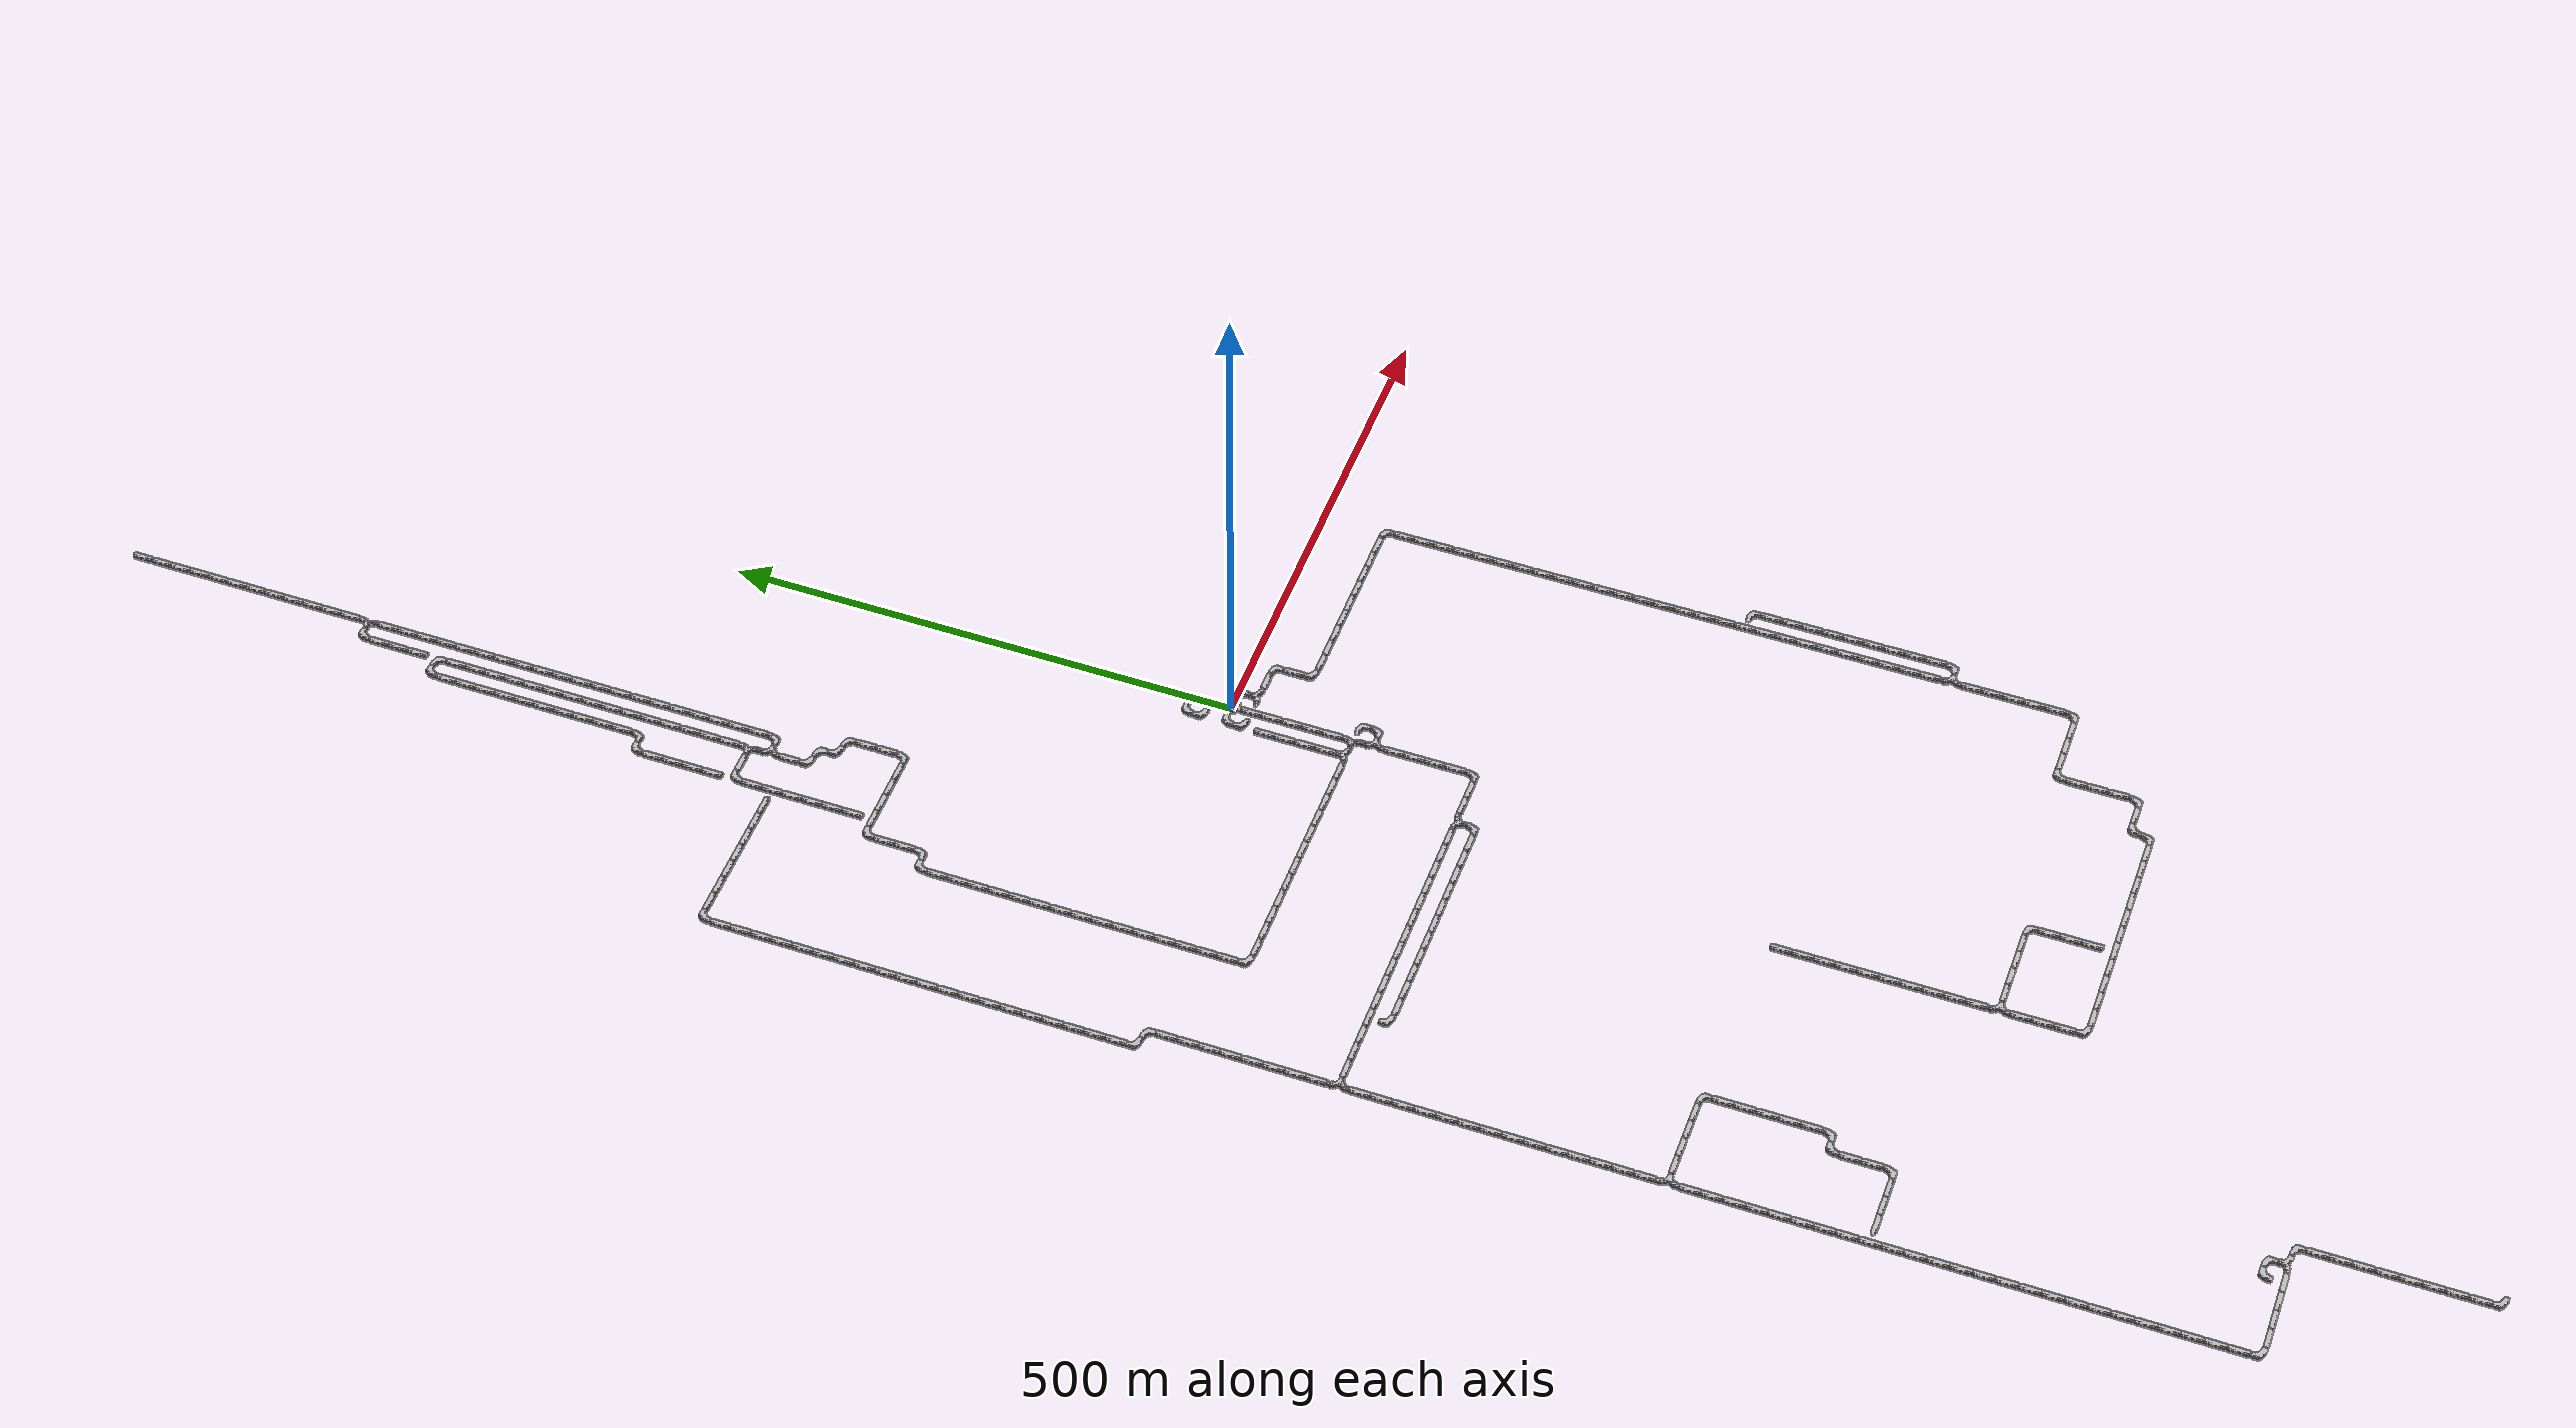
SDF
<sdf version="1.6">
 <world name="cave_8000_32">
  <include>
   <static>true</static>
   <name>cave_0_0</name>
   <pose>0 0 0 0 0 -1.5707963267948966</pose>
   <uri>model://cave_4way_20m</uri>
  </include>
  <include>
   <static>true</static>
   <name>cave_1_0</name>
   <pose>20 0 0 0 0 3.141592653589793</pose>
   <uri>model://cave_L_20m</uri>
  </include>
  <include>
   <static>true</static>
   <name>cave_1_-1</name>
   <pose>20 -20 0 0 0 0.0</pose>
   <uri>model://cave_3way_20m</uri>
  </include>
  <include>
   <static>true</static>
   <name>cave_2_-1</name>
   <pose>40 -20 0 0 0 1.5707963267948966</pose>
   <uri>model://cave_straight_20m</uri>
  </include>
  <include>
   <static>true</static>
   <name>cave_3_-1</name>
   <pose>60 -20 0 0 0 3.141592653589793</pose>
   <uri>model://cave_L_20m</uri>
  </include>
  <include>
   <static>true</static>
   <name>cave_3_-2</name>
   <pose>60 -40 0 0 0 0.0</pose>
   <uri>model://cave_straight_20m</uri>
  </include>
  <include>
   <static>true</static>
   <name>cave_3_-3</name>
   <pose>60 -60 0 0 0 0.0</pose>
   <uri>model://cave_L_20m</uri>
  </include>
  <include>
   <static>true</static>
   <name>cave_4_-3</name>
   <pose>80 -60 0 0 0 1.5707963267948966</pose>
   <uri>model://cave_straight_20m</uri>
  </include>
  <include>
   <static>true</static>
   <name>cave_5_-3</name>
   <pose>100 -60 0 0 0 1.5707963267948966</pose>
   <uri>model://cave_straight_20m</uri>
  </include>
  <include>
   <static>true</static>
   <name>cave_6_-3</name>
   <pose>120 -60 0 0 0 1.5707963267948966</pose>
   <uri>model://cave_straight_20m</uri>
  </include>
  <include>
   <static>true</static>
   <name>cave_7_-3</name>
   <pose>140 -60 0 0 0 1.5707963267948966</pose>
   <uri>model://cave_straight_20m</uri>
  </include>
  <include>
   <static>true</static>
   <name>cave_8_-3</name>
   <pose>160 -60 0 0 0 1.5707963267948966</pose>
   <uri>model://cave_straight_20m</uri>
  </include>
  <include>
   <static>true</static>
   <name>cave_9_-3</name>
   <pose>180 -60 0 0 0 1.5707963267948966</pose>
   <uri>model://cave_straight_20m</uri>
  </include>
  <include>
   <static>true</static>
   <name>cave_10_-3</name>
   <pose>200 -60 0 0 0 1.5707963267948966</pose>
   <uri>model://cave_straight_20m</uri>
  </include>
  <include>
   <static>true</static>
   <name>cave_11_-3</name>
   <pose>220 -60 0 0 0 1.5707963267948966</pose>
   <uri>model://cave_straight_20m</uri>
  </include>
  <include>
   <static>true</static>
   <name>cave_12_-3</name>
   <pose>240 -60 0 0 0 1.5707963267948966</pose>
   <uri>model://cave_straight_20m</uri>
  </include>
  <include>
   <static>true</static>
   <name>cave_13_-3</name>
   <pose>260 -60 0 0 0 3.141592653589793</pose>
   <uri>model://cave_L_20m</uri>
  </include>
  <include>
   <static>true</static>
   <name>cave_13_-4</name>
   <pose>260 -80 0 0 0 0.0</pose>
   <uri>model://cave_straight_20m</uri>
  </include>
  <include>
   <static>true</static>
   <name>cave_13_-5</name>
   <pose>260 -100 0 0 0 0.0</pose>
   <uri>model://cave_straight_20m</uri>
  </include>
  <include>
   <static>true</static>
   <name>cave_13_-6</name>
   <pose>260 -120 0 0 0 0.0</pose>
   <uri>model://cave_straight_20m</uri>
  </include>
  <include>
   <static>true</static>
   <name>cave_13_-7</name>
   <pose>260 -140 0 0 0 0.0</pose>
   <uri>model://cave_straight_20m</uri>
  </include>
  <include>
   <static>true</static>
   <name>cave_13_-8</name>
   <pose>260 -160 0 0 0 0.0</pose>
   <uri>model://cave_straight_20m</uri>
  </include>
  <include>
   <static>true</static>
   <name>cave_13_-9</name>
   <pose>260 -180 0 0 0 0.0</pose>
   <uri>model://cave_straight_20m</uri>
  </include>
  <include>
   <static>true</static>
   <name>cave_13_-10</name>
   <pose>260 -200 0 0 0 0.0</pose>
   <uri>model://cave_straight_20m</uri>
  </include>
  <include>
   <static>true</static>
   <name>cave_13_-11</name>
   <pose>260 -220 0 0 0 0.0</pose>
   <uri>model://cave_straight_20m</uri>
  </include>
  <include>
   <static>true</static>
   <name>cave_13_-12</name>
   <pose>260 -240 0 0 0 0.0</pose>
   <uri>model://cave_straight_20m</uri>
  </include>
  <include>
   <static>true</static>
   <name>cave_13_-13</name>
   <pose>260 -260 0 0 0 0.0</pose>
   <uri>model://cave_straight_20m</uri>
  </include>
  <include>
   <static>true</static>
   <name>cave_13_-14</name>
   <pose>260 -280 0 0 0 0.0</pose>
   <uri>model://cave_straight_20m</uri>
  </include>
  <include>
   <static>true</static>
   <name>cave_13_-15</name>
   <pose>260 -300 0 0 0 0.0</pose>
   <uri>model://cave_straight_20m</uri>
  </include>
  <include>
   <static>true</static>
   <name>cave_13_-16</name>
   <pose>260 -320 0 0 0 0.0</pose>
   <uri>model://cave_straight_20m</uri>
  </include>
  <include>
   <static>true</static>
   <name>cave_13_-17</name>
   <pose>260 -340 0 0 0 0.0</pose>
   <uri>model://cave_straight_20m</uri>
  </include>
  <include>
   <static>true</static>
   <name>cave_13_-18</name>
   <pose>260 -360 0 0 0 0.0</pose>
   <uri>model://cave_straight_20m</uri>
  </include>
  <include>
   <static>true</static>
   <name>cave_13_-19</name>
   <pose>260 -380 0 0 0 0.0</pose>
   <uri>model://cave_straight_20m</uri>
  </include>
  <include>
   <static>true</static>
   <name>cave_13_-20</name>
   <pose>260 -400 0 0 0 0.0</pose>
   <uri>model://cave_straight_20m</uri>
  </include>
  <include>
   <static>true</static>
   <name>cave_13_-21</name>
   <pose>260 -420 0 0 0 0.0</pose>
   <uri>model://cave_straight_20m</uri>
  </include>
  <include>
   <static>true</static>
   <name>cave_13_-22</name>
   <pose>260 -440 0 0 0 0.0</pose>
   <uri>model://cave_straight_20m</uri>
  </include>
  <include>
   <static>true</static>
   <name>cave_13_-23</name>
   <pose>260 -460 0 0 0 0.0</pose>
   <uri>model://cave_straight_20m</uri>
  </include>
  <include>
   <static>true</static>
   <name>cave_13_-24</name>
   <pose>260 -480 0 0 0 0.0</pose>
   <uri>model://cave_straight_20m</uri>
  </include>
  <include>
   <static>true</static>
   <name>cave_13_-25</name>
   <pose>260 -500 0 0 0 0.0</pose>
   <uri>model://cave_straight_20m</uri>
  </include>
  <include>
   <static>true</static>
   <name>cave_13_-26</name>
   <pose>260 -520 0 0 0 0.0</pose>
   <uri>model://cave_straight_20m</uri>
  </include>
  <include>
   <static>true</static>
   <name>cave_13_-27</name>
   <pose>260 -540 0 0 0 0.0</pose>
   <uri>model://cave_straight_20m</uri>
  </include>
  <include>
   <static>true</static>
   <name>cave_13_-28</name>
   <pose>260 -560 0 0 0 0.0</pose>
   <uri>model://cave_straight_20m</uri>
  </include>
  <include>
   <static>true</static>
   <name>cave_13_-29</name>
   <pose>260 -580 0 0 0 0.0</pose>
   <uri>model://cave_straight_20m</uri>
  </include>
  <include>
   <static>true</static>
   <name>cave_13_-30</name>
   <pose>260 -600 0 0 0 0.0</pose>
   <uri>model://cave_straight_20m</uri>
  </include>
  <include>
   <static>true</static>
   <name>cave_13_-31</name>
   <pose>260 -620 0 0 0 -1.5707963267948966</pose>
   <uri>model://cave_3way_20m</uri>
  </include>
  <include>
   <static>true</static>
   <name>cave_14_-31</name>
   <pose>280 -620 0 0 0 1.5707963267948966</pose>
   <uri>model://cave_L_20m</uri>
  </include>
  <include>
   <static>true</static>
   <name>cave_14_-30</name>
   <pose>280 -600 0 0 0 0.0</pose>
   <uri>model://cave_straight_20m</uri>
  </include>
  <include>
   <static>true</static>
   <name>cave_14_-29</name>
   <pose>280 -580 0 0 0 0.0</pose>
   <uri>model://cave_straight_20m</uri>
  </include>
  <include>
   <static>true</static>
   <name>cave_14_-28</name>
   <pose>280 -560 0 0 0 0.0</pose>
   <uri>model://cave_straight_20m</uri>
  </include>
  <include>
   <static>true</static>
   <name>cave_14_-27</name>
   <pose>280 -540 0 0 0 0.0</pose>
   <uri>model://cave_straight_20m</uri>
  </include>
  <include>
   <static>true</static>
   <name>cave_14_-26</name>
   <pose>280 -520 0 0 0 0.0</pose>
   <uri>model://cave_straight_20m</uri>
  </include>
  <include>
   <static>true</static>
   <name>cave_14_-25</name>
   <pose>280 -500 0 0 0 0.0</pose>
   <uri>model://cave_straight_20m</uri>
  </include>
  <include>
   <static>true</static>
   <name>cave_14_-24</name>
   <pose>280 -480 0 0 0 0.0</pose>
   <uri>model://cave_straight_20m</uri>
  </include>
  <include>
   <static>true</static>
   <name>cave_14_-23</name>
   <pose>280 -460 0 0 0 0.0</pose>
   <uri>model://cave_straight_20m</uri>
  </include>
  <include>
   <static>true</static>
   <name>cave_14_-22</name>
   <pose>280 -440 0 0 0 0.0</pose>
   <uri>model://cave_straight_20m</uri>
  </include>
  <include>
   <static>true</static>
   <name>cave_14_-21</name>
   <pose>280 -420 0 0 0 3.141592653589793</pose>
   <uri>model://cave_L_20m</uri>
  </include>
  <include>
   <static>true</static>
   <name>cave_13_-32</name>
   <pose>260 -640 0 0 0 0.0</pose>
   <uri>model://cave_straight_20m</uri>
  </include>
  <include>
   <static>true</static>
   <name>cave_13_-33</name>
   <pose>260 -660 0 0 0 0.0</pose>
   <uri>model://cave_straight_20m</uri>
  </include>
  <include>
   <static>true</static>
   <name>cave_13_-34</name>
   <pose>260 -680 0 0 0 0.0</pose>
   <uri>model://cave_straight_20m</uri>
  </include>
  <include>
   <static>true</static>
   <name>cave_13_-35</name>
   <pose>260 -700 0 0 0 0.0</pose>
   <uri>model://cave_straight_20m</uri>
  </include>
  <include>
   <static>true</static>
   <name>cave_13_-36</name>
   <pose>260 -720 0 0 0 0.0</pose>
   <uri>model://cave_straight_20m</uri>
  </include>
  <include>
   <static>true</static>
   <name>cave_13_-37</name>
   <pose>260 -740 0 0 0 1.5707963267948966</pose>
   <uri>model://cave_L_20m</uri>
  </include>
  <include>
   <static>true</static>
   <name>cave_12_-37</name>
   <pose>240 -740 0 0 0 1.5707963267948966</pose>
   <uri>model://cave_straight_20m</uri>
  </include>
  <include>
   <static>true</static>
   <name>cave_11_-37</name>
   <pose>220 -740 0 0 0 1.5707963267948966</pose>
   <uri>model://cave_straight_20m</uri>
  </include>
  <include>
   <static>true</static>
   <name>cave_10_-37</name>
   <pose>200 -740 0 0 0 1.5707963267948966</pose>
   <uri>model://cave_straight_20m</uri>
  </include>
  <include>
   <static>true</static>
   <name>cave_9_-37</name>
   <pose>180 -740 0 0 0 -1.5707963267948966</pose>
   <uri>model://cave_L_20m</uri>
  </include>
  <include>
   <static>true</static>
   <name>cave_9_-38</name>
   <pose>180 -760 0 0 0 0.0</pose>
   <uri>model://cave_straight_20m</uri>
  </include>
  <include>
   <static>true</static>
   <name>cave_9_-39</name>
   <pose>180 -780 0 0 0 0.0</pose>
   <uri>model://cave_straight_20m</uri>
  </include>
  <include>
   <static>true</static>
   <name>cave_9_-40</name>
   <pose>180 -800 0 0 0 0.0</pose>
   <uri>model://cave_straight_20m</uri>
  </include>
  <include>
   <static>true</static>
   <name>cave_9_-41</name>
   <pose>180 -820 0 0 0 1.5707963267948966</pose>
   <uri>model://cave_L_20m</uri>
  </include>
  <include>
   <static>true</static>
   <name>cave_8_-41</name>
   <pose>160 -820 0 0 0 1.5707963267948966</pose>
   <uri>model://cave_straight_20m</uri>
  </include>
  <include>
   <static>true</static>
   <name>cave_7_-41</name>
   <pose>140 -820 0 0 0 -1.5707963267948966</pose>
   <uri>model://cave_L_20m</uri>
  </include>
  <include>
   <static>true</static>
   <name>cave_7_-42</name>
   <pose>140 -840 0 0 0 1.5707963267948966</pose>
   <uri>model://cave_L_20m</uri>
  </include>
  <include>
   <static>true</static>
   <name>cave_6_-42</name>
   <pose>120 -840 0 0 0 1.5707963267948966</pose>
   <uri>model://cave_straight_20m</uri>
  </include>
  <include>
   <static>true</static>
   <name>cave_5_-42</name>
   <pose>100 -840 0 0 0 1.5707963267948966</pose>
   <uri>model://cave_straight_20m</uri>
  </include>
  <include>
   <static>true</static>
   <name>cave_4_-42</name>
   <pose>80 -840 0 0 0 1.5707963267948966</pose>
   <uri>model://cave_straight_20m</uri>
  </include>
  <include>
   <static>true</static>
   <name>cave_3_-42</name>
   <pose>60 -840 0 0 0 1.5707963267948966</pose>
   <uri>model://cave_straight_20m</uri>
  </include>
  <include>
   <static>true</static>
   <name>cave_2_-42</name>
   <pose>40 -840 0 0 0 1.5707963267948966</pose>
   <uri>model://cave_straight_20m</uri>
  </include>
  <include>
   <static>true</static>
   <name>cave_1_-42</name>
   <pose>20 -840 0 0 0 1.5707963267948966</pose>
   <uri>model://cave_straight_20m</uri>
  </include>
  <include>
   <static>true</static>
   <name>cave_0_-42</name>
   <pose>0 -840 0 0 0 1.5707963267948966</pose>
   <uri>model://cave_straight_20m</uri>
  </include>
  <include>
   <static>true</static>
   <name>cave_-1_-42</name>
   <pose>-20 -840 0 0 0 1.5707963267948966</pose>
   <uri>model://cave_straight_20m</uri>
  </include>
  <include>
   <static>true</static>
   <name>cave_-2_-42</name>
   <pose>-40 -840 0 0 0 1.5707963267948966</pose>
   <uri>model://cave_straight_20m</uri>
  </include>
  <include>
   <static>true</static>
   <name>cave_-3_-42</name>
   <pose>-60 -840 0 0 0 1.5707963267948966</pose>
   <uri>model://cave_straight_20m</uri>
  </include>
  <include>
   <static>true</static>
   <name>cave_-4_-42</name>
   <pose>-80 -840 0 0 0 1.5707963267948966</pose>
   <uri>model://cave_straight_20m</uri>
  </include>
  <include>
   <static>true</static>
   <name>cave_-5_-42</name>
   <pose>-100 -840 0 0 0 0.0</pose>
   <uri>model://cave_L_20m</uri>
  </include>
  <include>
   <static>true</static>
   <name>cave_-5_-41</name>
   <pose>-100 -820 0 0 0 0.0</pose>
   <uri>model://cave_straight_20m</uri>
  </include>
  <include>
   <static>true</static>
   <name>cave_-5_-40</name>
   <pose>-100 -800 0 0 0 0.0</pose>
   <uri>model://cave_straight_20m</uri>
  </include>
  <include>
   <static>true</static>
   <name>cave_-5_-39</name>
   <pose>-100 -780 0 0 0 0.0</pose>
   <uri>model://cave_straight_20m</uri>
  </include>
  <include>
   <static>true</static>
   <name>cave_-5_-38</name>
   <pose>-100 -760 0 0 0 -1.5707963267948966</pose>
   <uri>model://cave_3way_20m</uri>
  </include>
  <include>
   <static>true</static>
   <name>cave_-4_-38</name>
   <pose>-80 -760 0 0 0 1.5707963267948966</pose>
   <uri>model://cave_straight_20m</uri>
  </include>
  <include>
   <static>true</static>
   <name>cave_-3_-38</name>
   <pose>-60 -760 0 0 0 1.5707963267948966</pose>
   <uri>model://cave_straight_20m</uri>
  </include>
  <include>
   <static>true</static>
   <name>cave_-2_-38</name>
   <pose>-40 -760 0 0 0 1.5707963267948966</pose>
   <uri>model://cave_straight_20m</uri>
  </include>
  <include>
   <static>true</static>
   <name>cave_-1_-38</name>
   <pose>-20 -760 0 0 0 1.5707963267948966</pose>
   <uri>model://cave_straight_20m</uri>
  </include>
  <include>
   <static>true</static>
   <name>cave_0_-38</name>
   <pose>0 -760 0 0 0 3.141592653589793</pose>
   <uri>model://cave_L_20m</uri>
  </include>
  <include>
   <static>true</static>
   <name>cave_0_-39</name>
   <pose>0 -780 0 0 0 0.0</pose>
   <uri>model://cave_straight_20m</uri>
  </include>
  <include>
   <static>true</static>
   <name>cave_0_-40</name>
   <pose>0 -800 0 0 0 0.0</pose>
   <uri>model://cave_straight_20m</uri>
  </include>
  <include>
   <static>true</static>
   <name>cave_0_-41</name>
   <pose>0 -820 0 0 0 0.0</pose>
   <uri>model://cave_straight_20m</uri>
  </include>
  <include>
   <static>true</static>
   <name>cave_-5_-37</name>
   <pose>-100 -740 0 0 0 0.0</pose>
   <uri>model://cave_straight_20m</uri>
  </include>
  <include>
   <static>true</static>
   <name>cave_-5_-36</name>
   <pose>-100 -720 0 0 0 0.0</pose>
   <uri>model://cave_straight_20m</uri>
  </include>
  <include>
   <static>true</static>
   <name>cave_-5_-35</name>
   <pose>-100 -700 0 0 0 0.0</pose>
   <uri>model://cave_straight_20m</uri>
  </include>
  <include>
   <static>true</static>
   <name>cave_-5_-34</name>
   <pose>-100 -680 0 0 0 0.0</pose>
   <uri>model://cave_straight_20m</uri>
  </include>
  <include>
   <static>true</static>
   <name>cave_-5_-33</name>
   <pose>-100 -660 0 0 0 0.0</pose>
   <uri>model://cave_straight_20m</uri>
  </include>
  <include>
   <static>true</static>
   <name>cave_-5_-32</name>
   <pose>-100 -640 0 0 0 0.0</pose>
   <uri>model://cave_straight_20m</uri>
  </include>
  <include>
   <static>true</static>
   <name>cave_-5_-31</name>
   <pose>-100 -620 0 0 0 0.0</pose>
   <uri>model://cave_straight_20m</uri>
  </include>
  <include>
   <static>true</static>
   <name>cave_-5_-30</name>
   <pose>-100 -600 0 0 0 0.0</pose>
   <uri>model://cave_straight_20m</uri>
  </include>
  <include>
   <static>true</static>
   <name>cave_-5_-29</name>
   <pose>-100 -580 0 0 0 0.0</pose>
   <uri>model://cave_straight_20m</uri>
  </include>
  <include>
   <static>true</static>
   <name>cave_-5_-28</name>
   <pose>-100 -560 0 0 0 0.0</pose>
   <uri>model://cave_straight_20m</uri>
  </include>
  <include>
   <static>true</static>
   <name>cave_0_-1</name>
   <pose>0 -20 0 0 0 0.0</pose>
   <uri>model://cave_straight_20m</uri>
  </include>
  <include>
   <static>true</static>
   <name>cave_0_-2</name>
   <pose>0 -40 0 0 0 0.0</pose>
   <uri>model://cave_straight_20m</uri>
  </include>
  <include>
   <static>true</static>
   <name>cave_0_-3</name>
   <pose>0 -60 0 0 0 0.0</pose>
   <uri>model://cave_straight_20m</uri>
  </include>
  <include>
   <static>true</static>
   <name>cave_0_-4</name>
   <pose>0 -80 0 0 0 0.0</pose>
   <uri>model://cave_straight_20m</uri>
  </include>
  <include>
   <static>true</static>
   <name>cave_0_-5</name>
   <pose>0 -100 0 0 0 0.0</pose>
   <uri>model://cave_straight_20m</uri>
  </include>
  <include>
   <static>true</static>
   <name>cave_0_-6</name>
   <pose>0 -120 0 0 0 1.5707963267948966</pose>
   <uri>model://cave_3way_20m</uri>
  </include>
  <include>
   <static>true</static>
   <name>cave_0_-7</name>
   <pose>0 -140 0 0 0 -1.5707963267948966</pose>
   <uri>model://cave_3way_20m</uri>
  </include>
  <include>
   <static>true</static>
   <name>cave_1_-7</name>
   <pose>20 -140 0 0 0 1.5707963267948966</pose>
   <uri>model://cave_L_20m</uri>
  </include>
  <include>
   <static>true</static>
   <name>cave_1_-6</name>
   <pose>20 -120 0 0 0 3.141592653589793</pose>
   <uri>model://cave_L_20m</uri>
  </include>
  <include>
   <static>true</static>
   <name>cave_0_-8</name>
   <pose>0 -160 0 0 0 0.0</pose>
   <uri>model://cave_straight_20m</uri>
  </include>
  <include>
   <static>true</static>
   <name>cave_0_-9</name>
   <pose>0 -180 0 0 0 0.0</pose>
   <uri>model://cave_straight_20m</uri>
  </include>
  <include>
   <static>true</static>
   <name>cave_0_-10</name>
   <pose>0 -200 0 0 0 0.0</pose>
   <uri>model://cave_straight_20m</uri>
  </include>
  <include>
   <static>true</static>
   <name>cave_0_-11</name>
   <pose>0 -220 0 0 0 0.0</pose>
   <uri>model://cave_straight_20m</uri>
  </include>
  <include>
   <static>true</static>
   <name>cave_0_-12</name>
   <pose>0 -240 0 0 0 1.5707963267948966</pose>
   <uri>model://cave_L_20m</uri>
  </include>
  <include>
   <static>true</static>
   <name>cave_-1_-12</name>
   <pose>-20 -240 0 0 0 1.5707963267948966</pose>
   <uri>model://cave_straight_20m</uri>
  </include>
  <include>
   <static>true</static>
   <name>cave_-2_-12</name>
   <pose>-40 -240 0 0 0 1.5707963267948966</pose>
   <uri>model://cave_straight_20m</uri>
  </include>
  <include>
   <static>true</static>
   <name>cave_-3_-12</name>
   <pose>-60 -240 0 0 0 3.141592653589793</pose>
   <uri>model://cave_3way_20m</uri>
  </include>
  <include>
   <static>true</static>
   <name>cave_-3_-13</name>
   <pose>-60 -260 0 0 0 1.5707963267948966</pose>
   <uri>model://cave_L_20m</uri>
  </include>
  <include>
   <static>true</static>
   <name>cave_-4_-13</name>
   <pose>-80 -260 0 0 0 1.5707963267948966</pose>
   <uri>model://cave_straight_20m</uri>
  </include>
  <include>
   <static>true</static>
   <name>cave_-5_-13</name>
   <pose>-100 -260 0 0 0 1.5707963267948966</pose>
   <uri>model://cave_straight_20m</uri>
  </include>
  <include>
   <static>true</static>
   <name>cave_-6_-13</name>
   <pose>-120 -260 0 0 0 1.5707963267948966</pose>
   <uri>model://cave_straight_20m</uri>
  </include>
  <include>
   <static>true</static>
   <name>cave_-7_-13</name>
   <pose>-140 -260 0 0 0 1.5707963267948966</pose>
   <uri>model://cave_straight_20m</uri>
  </include>
  <include>
   <static>true</static>
   <name>cave_-8_-13</name>
   <pose>-160 -260 0 0 0 1.5707963267948966</pose>
   <uri>model://cave_straight_20m</uri>
  </include>
  <include>
   <static>true</static>
   <name>cave_-9_-13</name>
   <pose>-180 -260 0 0 0 1.5707963267948966</pose>
   <uri>model://cave_straight_20m</uri>
  </include>
  <include>
   <static>true</static>
   <name>cave_-10_-13</name>
   <pose>-200 -260 0 0 0 1.5707963267948966</pose>
   <uri>model://cave_straight_20m</uri>
  </include>
  <include>
   <static>true</static>
   <name>cave_-11_-13</name>
   <pose>-220 -260 0 0 0 1.5707963267948966</pose>
   <uri>model://cave_straight_20m</uri>
  </include>
  <include>
   <static>true</static>
   <name>cave_-12_-13</name>
   <pose>-240 -260 0 0 0 1.5707963267948966</pose>
   <uri>model://cave_straight_20m</uri>
  </include>
  <include>
   <static>true</static>
   <name>cave_-13_-13</name>
   <pose>-260 -260 0 0 0 1.5707963267948966</pose>
   <uri>model://cave_straight_20m</uri>
  </include>
  <include>
   <static>true</static>
   <name>cave_-14_-13</name>
   <pose>-280 -260 0 0 0 1.5707963267948966</pose>
   <uri>model://cave_straight_20m</uri>
  </include>
  <include>
   <static>true</static>
   <name>cave_-15_-13</name>
   <pose>-300 -260 0 0 0 0.0</pose>
   <uri>model://cave_L_20m</uri>
  </include>
  <include>
   <static>true</static>
   <name>cave_-4_-12</name>
   <pose>-80 -240 0 0 0 1.5707963267948966</pose>
   <uri>model://cave_straight_20m</uri>
  </include>
  <include>
   <static>true</static>
   <name>cave_-5_-12</name>
   <pose>-100 -240 0 0 0 1.5707963267948966</pose>
   <uri>model://cave_straight_20m</uri>
  </include>
  <include>
   <static>true</static>
   <name>cave_-6_-12</name>
   <pose>-120 -240 0 0 0 1.5707963267948966</pose>
   <uri>model://cave_straight_20m</uri>
  </include>
  <include>
   <static>true</static>
   <name>cave_-7_-12</name>
   <pose>-140 -240 0 0 0 1.5707963267948966</pose>
   <uri>model://cave_straight_20m</uri>
  </include>
  <include>
   <static>true</static>
   <name>cave_-8_-12</name>
   <pose>-160 -240 0 0 0 1.5707963267948966</pose>
   <uri>model://cave_straight_20m</uri>
  </include>
  <include>
   <static>true</static>
   <name>cave_-9_-12</name>
   <pose>-180 -240 0 0 0 1.5707963267948966</pose>
   <uri>model://cave_straight_20m</uri>
  </include>
  <include>
   <static>true</static>
   <name>cave_-10_-12</name>
   <pose>-200 -240 0 0 0 1.5707963267948966</pose>
   <uri>model://cave_straight_20m</uri>
  </include>
  <include>
   <static>true</static>
   <name>cave_-11_-12</name>
   <pose>-220 -240 0 0 0 1.5707963267948966</pose>
   <uri>model://cave_straight_20m</uri>
  </include>
  <include>
   <static>true</static>
   <name>cave_-12_-12</name>
   <pose>-240 -240 0 0 0 1.5707963267948966</pose>
   <uri>model://cave_straight_20m</uri>
  </include>
  <include>
   <static>true</static>
   <name>cave_-13_-12</name>
   <pose>-260 -240 0 0 0 1.5707963267948966</pose>
   <uri>model://cave_straight_20m</uri>
  </include>
  <include>
   <static>true</static>
   <name>cave_-14_-12</name>
   <pose>-280 -240 0 0 0 1.5707963267948966</pose>
   <uri>model://cave_straight_20m</uri>
  </include>
  <include>
   <static>true</static>
   <name>cave_-15_-12</name>
   <pose>-300 -240 0 0 0 1.5707963267948966</pose>
   <uri>model://cave_straight_20m</uri>
  </include>
  <include>
   <static>true</static>
   <name>cave_-16_-12</name>
   <pose>-320 -240 0 0 0 1.5707963267948966</pose>
   <uri>model://cave_straight_20m</uri>
  </include>
  <include>
   <static>true</static>
   <name>cave_-17_-12</name>
   <pose>-340 -240 0 0 0 1.5707963267948966</pose>
   <uri>model://cave_straight_20m</uri>
  </include>
  <include>
   <static>true</static>
   <name>cave_-18_-12</name>
   <pose>-360 -240 0 0 0 1.5707963267948966</pose>
   <uri>model://cave_straight_20m</uri>
  </include>
  <include>
   <static>true</static>
   <name>cave_-19_-12</name>
   <pose>-380 -240 0 0 0 -1.5707963267948966</pose>
   <uri>model://cave_3way_20m</uri>
  </include>
  <include>
   <static>true</static>
   <name>cave_-19_-13</name>
   <pose>-380 -260 0 0 0 0.0</pose>
   <uri>model://cave_straight_20m</uri>
  </include>
  <include>
   <static>true</static>
   <name>cave_-19_-14</name>
   <pose>-380 -280 0 0 0 0.0</pose>
   <uri>model://cave_straight_20m</uri>
  </include>
  <include>
   <static>true</static>
   <name>cave_-19_-15</name>
   <pose>-380 -300 0 0 0 0.0</pose>
   <uri>model://cave_straight_20m</uri>
  </include>
  <include>
   <static>true</static>
   <name>cave_-19_-16</name>
   <pose>-380 -320 0 0 0 0.0</pose>
   <uri>model://cave_straight_20m</uri>
  </include>
  <include>
   <static>true</static>
   <name>cave_-19_-17</name>
   <pose>-380 -340 0 0 0 0.0</pose>
   <uri>model://cave_straight_20m</uri>
  </include>
  <include>
   <static>true</static>
   <name>cave_-19_-18</name>
   <pose>-380 -360 0 0 0 0.0</pose>
   <uri>model://cave_straight_20m</uri>
  </include>
  <include>
   <static>true</static>
   <name>cave_-19_-19</name>
   <pose>-380 -380 0 0 0 0.0</pose>
   <uri>model://cave_straight_20m</uri>
  </include>
  <include>
   <static>true</static>
   <name>cave_-19_-20</name>
   <pose>-380 -400 0 0 0 0.0</pose>
   <uri>model://cave_straight_20m</uri>
  </include>
  <include>
   <static>true</static>
   <name>cave_-19_-21</name>
   <pose>-380 -420 0 0 0 0.0</pose>
   <uri>model://cave_straight_20m</uri>
  </include>
  <include>
   <static>true</static>
   <name>cave_-19_-22</name>
   <pose>-380 -440 0 0 0 0.0</pose>
   <uri>model://cave_straight_20m</uri>
  </include>
  <include>
   <static>true</static>
   <name>cave_-19_-23</name>
   <pose>-380 -460 0 0 0 0.0</pose>
   <uri>model://cave_straight_20m</uri>
  </include>
  <include>
   <static>true</static>
   <name>cave_-19_-24</name>
   <pose>-380 -480 0 0 0 0.0</pose>
   <uri>model://cave_straight_20m</uri>
  </include>
  <include>
   <static>true</static>
   <name>cave_-19_-25</name>
   <pose>-380 -500 0 0 0 0.0</pose>
   <uri>model://cave_straight_20m</uri>
  </include>
  <include>
   <static>true</static>
   <name>cave_-19_-26</name>
   <pose>-380 -520 0 0 0 0.0</pose>
   <uri>model://cave_straight_20m</uri>
  </include>
  <include>
   <static>true</static>
   <name>cave_-19_-27</name>
   <pose>-380 -540 0 0 0 -1.5707963267948966</pose>
   <uri>model://cave_3way_20m</uri>
  </include>
  <include>
   <static>true</static>
   <name>cave_-18_-27</name>
   <pose>-360 -540 0 0 0 1.5707963267948966</pose>
   <uri>model://cave_straight_20m</uri>
  </include>
  <include>
   <static>true</static>
   <name>cave_-17_-27</name>
   <pose>-340 -540 0 0 0 1.5707963267948966</pose>
   <uri>model://cave_straight_20m</uri>
  </include>
  <include>
   <static>true</static>
   <name>cave_-16_-27</name>
   <pose>-320 -540 0 0 0 1.5707963267948966</pose>
   <uri>model://cave_straight_20m</uri>
  </include>
  <include>
   <static>true</static>
   <name>cave_-15_-27</name>
   <pose>-300 -540 0 0 0 1.5707963267948966</pose>
   <uri>model://cave_straight_20m</uri>
  </include>
  <include>
   <static>true</static>
   <name>cave_-14_-27</name>
   <pose>-280 -540 0 0 0 3.141592653589793</pose>
   <uri>model://cave_L_20m</uri>
  </include>
  <include>
   <static>true</static>
   <name>cave_-14_-28</name>
   <pose>-280 -560 0 0 0 0.0</pose>
   <uri>model://cave_straight_20m</uri>
  </include>
  <include>
   <static>true</static>
   <name>cave_-14_-29</name>
   <pose>-280 -580 0 0 0 0.0</pose>
   <uri>model://cave_straight_20m</uri>
  </include>
  <include>
   <static>true</static>
   <name>cave_-14_-30</name>
   <pose>-280 -600 0 0 0 0.0</pose>
   <uri>model://cave_straight_20m</uri>
  </include>
  <include>
   <static>true</static>
   <name>cave_-14_-31</name>
   <pose>-280 -620 0 0 0 0.0</pose>
   <uri>model://cave_straight_20m</uri>
  </include>
  <include>
   <static>true</static>
   <name>cave_-14_-32</name>
   <pose>-280 -640 0 0 0 0.0</pose>
   <uri>model://cave_straight_20m</uri>
  </include>
  <include>
   <static>true</static>
   <name>cave_-14_-33</name>
   <pose>-280 -660 0 0 0 1.5707963267948966</pose>
   <uri>model://cave_L_20m</uri>
  </include>
  <include>
   <static>true</static>
   <name>cave_-15_-33</name>
   <pose>-300 -660 0 0 0 -1.5707963267948966</pose>
   <uri>model://cave_L_20m</uri>
  </include>
  <include>
   <static>true</static>
   <name>cave_-15_-34</name>
   <pose>-300 -680 0 0 0 0.0</pose>
   <uri>model://cave_straight_20m</uri>
  </include>
  <include>
   <static>true</static>
   <name>cave_-15_-35</name>
   <pose>-300 -700 0 0 0 0.0</pose>
   <uri>model://cave_straight_20m</uri>
  </include>
  <include>
   <static>true</static>
   <name>cave_-15_-36</name>
   <pose>-300 -720 0 0 0 1.5707963267948966</pose>
   <uri>model://cave_L_20m</uri>
  </include>
  <include>
   <static>true</static>
   <name>cave_-16_-36</name>
   <pose>-320 -720 0 0 0 1.5707963267948966</pose>
   <uri>model://cave_straight_20m</uri>
  </include>
  <include>
   <static>true</static>
   <name>cave_-17_-36</name>
   <pose>-340 -720 0 0 0 1.5707963267948966</pose>
   <uri>model://cave_straight_20m</uri>
  </include>
  <include>
   <static>true</static>
   <name>cave_-18_-36</name>
   <pose>-360 -720 0 0 0 1.5707963267948966</pose>
   <uri>model://cave_straight_20m</uri>
  </include>
  <include>
   <static>true</static>
   <name>cave_-19_-28</name>
   <pose>-380 -560 0 0 0 0.0</pose>
   <uri>model://cave_straight_20m</uri>
  </include>
  <include>
   <static>true</static>
   <name>cave_-19_-29</name>
   <pose>-380 -580 0 0 0 0.0</pose>
   <uri>model://cave_straight_20m</uri>
  </include>
  <include>
   <static>true</static>
   <name>cave_-19_-30</name>
   <pose>-380 -600 0 0 0 0.0</pose>
   <uri>model://cave_straight_20m</uri>
  </include>
  <include>
   <static>true</static>
   <name>cave_-19_-31</name>
   <pose>-380 -620 0 0 0 0.0</pose>
   <uri>model://cave_straight_20m</uri>
  </include>
  <include>
   <static>true</static>
   <name>cave_-19_-32</name>
   <pose>-380 -640 0 0 0 0.0</pose>
   <uri>model://cave_straight_20m</uri>
  </include>
  <include>
   <static>true</static>
   <name>cave_-19_-33</name>
   <pose>-380 -660 0 0 0 0.0</pose>
   <uri>model://cave_straight_20m</uri>
  </include>
  <include>
   <static>true</static>
   <name>cave_-19_-34</name>
   <pose>-380 -680 0 0 0 0.0</pose>
   <uri>model://cave_straight_20m</uri>
  </include>
  <include>
   <static>true</static>
   <name>cave_-19_-35</name>
   <pose>-380 -700 0 0 0 0.0</pose>
   <uri>model://cave_straight_20m</uri>
  </include>
  <include>
   <static>true</static>
   <name>cave_-19_-36</name>
   <pose>-380 -720 0 0 0 0.0</pose>
   <uri>model://cave_straight_20m</uri>
  </include>
  <include>
   <static>true</static>
   <name>cave_-19_-37</name>
   <pose>-380 -740 0 0 0 0.0</pose>
   <uri>model://cave_straight_20m</uri>
  </include>
  <include>
   <static>true</static>
   <name>cave_-19_-38</name>
   <pose>-380 -760 0 0 0 0.0</pose>
   <uri>model://cave_straight_20m</uri>
  </include>
  <include>
   <static>true</static>
   <name>cave_-19_-39</name>
   <pose>-380 -780 0 0 0 0.0</pose>
   <uri>model://cave_straight_20m</uri>
  </include>
  <include>
   <static>true</static>
   <name>cave_-19_-40</name>
   <pose>-380 -800 0 0 0 0.0</pose>
   <uri>model://cave_straight_20m</uri>
  </include>
  <include>
   <static>true</static>
   <name>cave_-19_-41</name>
   <pose>-380 -820 0 0 0 0.0</pose>
   <uri>model://cave_straight_20m</uri>
  </include>
  <include>
   <static>true</static>
   <name>cave_-19_-42</name>
   <pose>-380 -840 0 0 0 0.0</pose>
   <uri>model://cave_straight_20m</uri>
  </include>
  <include>
   <static>true</static>
   <name>cave_-19_-43</name>
   <pose>-380 -860 0 0 0 0.0</pose>
   <uri>model://cave_straight_20m</uri>
  </include>
  <include>
   <static>true</static>
   <name>cave_-19_-44</name>
   <pose>-380 -880 0 0 0 0.0</pose>
   <uri>model://cave_straight_20m</uri>
  </include>
  <include>
   <static>true</static>
   <name>cave_-19_-45</name>
   <pose>-380 -900 0 0 0 0.0</pose>
   <uri>model://cave_straight_20m</uri>
  </include>
  <include>
   <static>true</static>
   <name>cave_-19_-46</name>
   <pose>-380 -920 0 0 0 0.0</pose>
   <uri>model://cave_straight_20m</uri>
  </include>
  <include>
   <static>true</static>
   <name>cave_-19_-47</name>
   <pose>-380 -940 0 0 0 0.0</pose>
   <uri>model://cave_straight_20m</uri>
  </include>
  <include>
   <static>true</static>
   <name>cave_-19_-48</name>
   <pose>-380 -960 0 0 0 0.0</pose>
   <uri>model://cave_straight_20m</uri>
  </include>
  <include>
   <static>true</static>
   <name>cave_-19_-49</name>
   <pose>-380 -980 0 0 0 0.0</pose>
   <uri>model://cave_straight_20m</uri>
  </include>
  <include>
   <static>true</static>
   <name>cave_-19_-50</name>
   <pose>-380 -1000 0 0 0 0.0</pose>
   <uri>model://cave_straight_20m</uri>
  </include>
  <include>
   <static>true</static>
   <name>cave_-19_-51</name>
   <pose>-380 -1020 0 0 0 0.0</pose>
   <uri>model://cave_straight_20m</uri>
  </include>
  <include>
   <static>true</static>
   <name>cave_-19_-52</name>
   <pose>-380 -1040 0 0 0 0.0</pose>
   <uri>model://cave_straight_20m</uri>
  </include>
  <include>
   <static>true</static>
   <name>cave_-19_-53</name>
   <pose>-380 -1060 0 0 0 0.0</pose>
   <uri>model://cave_L_20m</uri>
  </include>
  <include>
   <static>true</static>
   <name>cave_-18_-53</name>
   <pose>-360 -1060 0 0 0 1.5707963267948966</pose>
   <uri>model://cave_straight_20m</uri>
  </include>
  <include>
   <static>true</static>
   <name>cave_-17_-53</name>
   <pose>-340 -1060 0 0 0 1.5707963267948966</pose>
   <uri>model://cave_straight_20m</uri>
  </include>
  <include>
   <static>true</static>
   <name>cave_-16_-53</name>
   <pose>-320 -1060 0 0 0 1.5707963267948966</pose>
   <uri>model://cave_straight_20m</uri>
  </include>
  <include>
   <static>true</static>
   <name>cave_-15_-53</name>
   <pose>-300 -1060 0 0 0 1.5707963267948966</pose>
   <uri>model://cave_straight_20m</uri>
  </include>
  <include>
   <static>true</static>
   <name>cave_-14_-53</name>
   <pose>-280 -1060 0 0 0 0.0</pose>
   <uri>model://cave_3way_20m</uri>
  </include>
  <include>
   <static>true</static>
   <name>cave_-13_-53</name>
   <pose>-260 -1060 0 0 0 3.141592653589793</pose>
   <uri>model://cave_L_20m</uri>
  </include>
  <include>
   <static>true</static>
   <name>cave_-13_-54</name>
   <pose>-260 -1080 0 0 0 0.0</pose>
   <uri>model://cave_straight_20m</uri>
  </include>
  <include>
   <static>true</static>
   <name>cave_-13_-55</name>
   <pose>-260 -1100 0 0 0 0.0</pose>
   <uri>model://cave_straight_20m</uri>
  </include>
  <include>
   <static>true</static>
   <name>cave_-13_-56</name>
   <pose>-260 -1120 0 0 0 0.0</pose>
   <uri>model://cave_straight_20m</uri>
  </include>
  <include>
   <static>true</static>
   <name>cave_-13_-57</name>
   <pose>-260 -1140 0 0 0 0.0</pose>
   <uri>model://cave_straight_20m</uri>
  </include>
  <include>
   <static>true</static>
   <name>cave_-13_-58</name>
   <pose>-260 -1160 0 0 0 0.0</pose>
   <uri>model://cave_straight_20m</uri>
  </include>
  <include>
   <static>true</static>
   <name>cave_-13_-59</name>
   <pose>-260 -1180 0 0 0 0.0</pose>
   <uri>model://cave_straight_20m</uri>
  </include>
  <include>
   <static>true</static>
   <name>cave_-13_-60</name>
   <pose>-260 -1200 0 0 0 0.0</pose>
   <uri>model://cave_straight_20m</uri>
  </include>
  <include>
   <static>true</static>
   <name>cave_-13_-61</name>
   <pose>-260 -1220 0 0 0 0.0</pose>
   <uri>model://cave_straight_20m</uri>
  </include>
  <include>
   <static>true</static>
   <name>cave_-13_-62</name>
   <pose>-260 -1240 0 0 0 0.0</pose>
   <uri>model://cave_L_20m</uri>
  </include>
  <include>
   <static>true</static>
   <name>cave_-14_-52</name>
   <pose>-280 -1040 0 0 0 3.141592653589793</pose>
   <uri>model://cave_L_20m</uri>
  </include>
  <include>
   <static>true</static>
   <name>cave_-15_-52</name>
   <pose>-300 -1040 0 0 0 -1.5707963267948966</pose>
   <uri>model://cave_L_20m</uri>
  </include>
  <include>
   <static>true</static>
   <name>cave_-19_-11</name>
   <pose>-380 -220 0 0 0 0.0</pose>
   <uri>model://cave_straight_20m</uri>
  </include>
  <include>
   <static>true</static>
   <name>cave_-19_-10</name>
   <pose>-380 -200 0 0 0 0.0</pose>
   <uri>model://cave_straight_20m</uri>
  </include>
  <include>
   <static>true</static>
   <name>cave_-19_-9</name>
   <pose>-380 -180 0 0 0 0.0</pose>
   <uri>model://cave_straight_20m</uri>
  </include>
  <include>
   <static>true</static>
   <name>cave_-19_-8</name>
   <pose>-380 -160 0 0 0 0.0</pose>
   <uri>model://cave_straight_20m</uri>
  </include>
  <include>
   <static>true</static>
   <name>cave_-19_-7</name>
   <pose>-380 -140 0 0 0 0.0</pose>
   <uri>model://cave_straight_20m</uri>
  </include>
  <include>
   <static>true</static>
   <name>cave_-19_-6</name>
   <pose>-380 -120 0 0 0 0.0</pose>
   <uri>model://cave_straight_20m</uri>
  </include>
  <include>
   <static>true</static>
   <name>cave_-19_-5</name>
   <pose>-380 -100 0 0 0 0.0</pose>
   <uri>model://cave_straight_20m</uri>
  </include>
  <include>
   <static>true</static>
   <name>cave_-19_-4</name>
   <pose>-380 -80 0 0 0 0.0</pose>
   <uri>model://cave_straight_20m</uri>
  </include>
  <include>
   <static>true</static>
   <name>cave_-19_-3</name>
   <pose>-380 -60 0 0 0 3.141592653589793</pose>
   <uri>model://cave_L_20m</uri>
  </include>
  <include>
   <static>true</static>
   <name>cave_-20_-3</name>
   <pose>-400 -60 0 0 0 0.0</pose>
   <uri>model://cave_L_20m</uri>
  </include>
  <include>
   <static>true</static>
   <name>cave_-20_-2</name>
   <pose>-400 -40 0 0 0 0.0</pose>
   <uri>model://cave_straight_20m</uri>
  </include>
  <include>
   <static>true</static>
   <name>cave_-20_-1</name>
   <pose>-400 -20 0 0 0 0.0</pose>
   <uri>model://cave_straight_20m</uri>
  </include>
  <include>
   <static>true</static>
   <name>cave_-20_0</name>
   <pose>-400 0 0 0 0 0.0</pose>
   <uri>model://cave_straight_20m</uri>
  </include>
  <include>
   <static>true</static>
   <name>cave_-20_1</name>
   <pose>-400 20 0 0 0 0.0</pose>
   <uri>model://cave_straight_20m</uri>
  </include>
  <include>
   <static>true</static>
   <name>cave_-20_2</name>
   <pose>-400 40 0 0 0 0.0</pose>
   <uri>model://cave_straight_20m</uri>
  </include>
  <include>
   <static>true</static>
   <name>cave_-20_3</name>
   <pose>-400 60 0 0 0 0.0</pose>
   <uri>model://cave_straight_20m</uri>
  </include>
  <include>
   <static>true</static>
   <name>cave_-20_4</name>
   <pose>-400 80 0 0 0 0.0</pose>
   <uri>model://cave_straight_20m</uri>
  </include>
  <include>
   <static>true</static>
   <name>cave_-20_5</name>
   <pose>-400 100 0 0 0 0.0</pose>
   <uri>model://cave_straight_20m</uri>
  </include>
  <include>
   <static>true</static>
   <name>cave_-20_6</name>
   <pose>-400 120 0 0 0 0.0</pose>
   <uri>model://cave_straight_20m</uri>
  </include>
  <include>
   <static>true</static>
   <name>cave_-20_7</name>
   <pose>-400 140 0 0 0 0.0</pose>
   <uri>model://cave_straight_20m</uri>
  </include>
  <include>
   <static>true</static>
   <name>cave_-20_8</name>
   <pose>-400 160 0 0 0 0.0</pose>
   <uri>model://cave_straight_20m</uri>
  </include>
  <include>
   <static>true</static>
   <name>cave_-20_9</name>
   <pose>-400 180 0 0 0 0.0</pose>
   <uri>model://cave_straight_20m</uri>
  </include>
  <include>
   <static>true</static>
   <name>cave_-20_10</name>
   <pose>-400 200 0 0 0 0.0</pose>
   <uri>model://cave_straight_20m</uri>
  </include>
  <include>
   <static>true</static>
   <name>cave_-20_11</name>
   <pose>-400 220 0 0 0 0.0</pose>
   <uri>model://cave_straight_20m</uri>
  </include>
  <include>
   <static>true</static>
   <name>cave_-20_12</name>
   <pose>-400 240 0 0 0 0.0</pose>
   <uri>model://cave_straight_20m</uri>
  </include>
  <include>
   <static>true</static>
   <name>cave_-20_13</name>
   <pose>-400 260 0 0 0 0.0</pose>
   <uri>model://cave_straight_20m</uri>
  </include>
  <include>
   <static>true</static>
   <name>cave_-20_14</name>
   <pose>-400 280 0 0 0 0.0</pose>
   <uri>model://cave_straight_20m</uri>
  </include>
  <include>
   <static>true</static>
   <name>cave_-20_15</name>
   <pose>-400 300 0 0 0 0.0</pose>
   <uri>model://cave_straight_20m</uri>
  </include>
  <include>
   <static>true</static>
   <name>cave_-20_16</name>
   <pose>-400 320 0 0 0 0.0</pose>
   <uri>model://cave_straight_20m</uri>
  </include>
  <include>
   <static>true</static>
   <name>cave_-20_17</name>
   <pose>-400 340 0 0 0 0.0</pose>
   <uri>model://cave_straight_20m</uri>
  </include>
  <include>
   <static>true</static>
   <name>cave_-20_18</name>
   <pose>-400 360 0 0 0 -1.5707963267948966</pose>
   <uri>model://cave_L_20m</uri>
  </include>
  <include>
   <static>true</static>
   <name>cave_-19_18</name>
   <pose>-380 360 0 0 0 1.5707963267948966</pose>
   <uri>model://cave_straight_20m</uri>
  </include>
  <include>
   <static>true</static>
   <name>cave_-18_18</name>
   <pose>-360 360 0 0 0 1.5707963267948966</pose>
   <uri>model://cave_straight_20m</uri>
  </include>
  <include>
   <static>true</static>
   <name>cave_-17_18</name>
   <pose>-340 360 0 0 0 1.5707963267948966</pose>
   <uri>model://cave_straight_20m</uri>
  </include>
  <include>
   <static>true</static>
   <name>cave_-16_18</name>
   <pose>-320 360 0 0 0 1.5707963267948966</pose>
   <uri>model://cave_straight_20m</uri>
  </include>
  <include>
   <static>true</static>
   <name>cave_-15_18</name>
   <pose>-300 360 0 0 0 1.5707963267948966</pose>
   <uri>model://cave_straight_20m</uri>
  </include>
  <include>
   <static>true</static>
   <name>cave_-14_18</name>
   <pose>-280 360 0 0 0 1.5707963267948966</pose>
   <uri>model://cave_straight_20m</uri>
  </include>
  <include>
   <static>true</static>
   <name>cave_-13_18</name>
   <pose>-260 360 0 0 0 1.5707963267948966</pose>
   <uri>model://cave_straight_20m</uri>
  </include>
  <include>
   <static>true</static>
   <name>cave_-1_-6</name>
   <pose>-20 -120 0 0 0 0.0</pose>
   <uri>model://cave_3way_20m</uri>
  </include>
  <include>
   <static>true</static>
   <name>cave_-2_-6</name>
   <pose>-40 -120 0 0 0 1.5707963267948966</pose>
   <uri>model://cave_straight_20m</uri>
  </include>
  <include>
   <static>true</static>
   <name>cave_-3_-6</name>
   <pose>-60 -120 0 0 0 1.5707963267948966</pose>
   <uri>model://cave_straight_20m</uri>
  </include>
  <include>
   <static>true</static>
   <name>cave_-4_-6</name>
   <pose>-80 -120 0 0 0 1.5707963267948966</pose>
   <uri>model://cave_straight_20m</uri>
  </include>
  <include>
   <static>true</static>
   <name>cave_-5_-6</name>
   <pose>-100 -120 0 0 0 1.5707963267948966</pose>
   <uri>model://cave_straight_20m</uri>
  </include>
  <include>
   <static>true</static>
   <name>cave_-6_-6</name>
   <pose>-120 -120 0 0 0 1.5707963267948966</pose>
   <uri>model://cave_straight_20m</uri>
  </include>
  <include>
   <static>true</static>
   <name>cave_-7_-6</name>
   <pose>-140 -120 0 0 0 1.5707963267948966</pose>
   <uri>model://cave_straight_20m</uri>
  </include>
  <include>
   <static>true</static>
   <name>cave_-8_-6</name>
   <pose>-160 -120 0 0 0 1.5707963267948966</pose>
   <uri>model://cave_straight_20m</uri>
  </include>
  <include>
   <static>true</static>
   <name>cave_-9_-6</name>
   <pose>-180 -120 0 0 0 1.5707963267948966</pose>
   <uri>model://cave_straight_20m</uri>
  </include>
  <include>
   <static>true</static>
   <name>cave_-10_-6</name>
   <pose>-200 -120 0 0 0 1.5707963267948966</pose>
   <uri>model://cave_straight_20m</uri>
  </include>
  <include>
   <static>true</static>
   <name>cave_-11_-6</name>
   <pose>-220 -120 0 0 0 1.5707963267948966</pose>
   <uri>model://cave_straight_20m</uri>
  </include>
  <include>
   <static>true</static>
   <name>cave_-12_-6</name>
   <pose>-240 -120 0 0 0 1.5707963267948966</pose>
   <uri>model://cave_straight_20m</uri>
  </include>
  <include>
   <static>true</static>
   <name>cave_-13_-6</name>
   <pose>-260 -120 0 0 0 1.5707963267948966</pose>
   <uri>model://cave_straight_20m</uri>
  </include>
  <include>
   <static>true</static>
   <name>cave_-14_-6</name>
   <pose>-280 -120 0 0 0 0.0</pose>
   <uri>model://cave_L_20m</uri>
  </include>
  <include>
   <static>true</static>
   <name>cave_-14_-5</name>
   <pose>-280 -100 0 0 0 0.0</pose>
   <uri>model://cave_straight_20m</uri>
  </include>
  <include>
   <static>true</static>
   <name>cave_-14_-4</name>
   <pose>-280 -80 0 0 0 0.0</pose>
   <uri>model://cave_straight_20m</uri>
  </include>
  <include>
   <static>true</static>
   <name>cave_-14_-3</name>
   <pose>-280 -60 0 0 0 0.0</pose>
   <uri>model://cave_straight_20m</uri>
  </include>
  <include>
   <static>true</static>
   <name>cave_-14_-2</name>
   <pose>-280 -40 0 0 0 0.0</pose>
   <uri>model://cave_straight_20m</uri>
  </include>
  <include>
   <static>true</static>
   <name>cave_-14_-1</name>
   <pose>-280 -20 0 0 0 0.0</pose>
   <uri>model://cave_straight_20m</uri>
  </include>
  <include>
   <static>true</static>
   <name>cave_-14_0</name>
   <pose>-280 0 0 0 0 0.0</pose>
   <uri>model://cave_straight_20m</uri>
  </include>
  <include>
   <static>true</static>
   <name>cave_-14_1</name>
   <pose>-280 20 0 0 0 0.0</pose>
   <uri>model://cave_straight_20m</uri>
  </include>
  <include>
   <static>true</static>
   <name>cave_-14_2</name>
   <pose>-280 40 0 0 0 0.0</pose>
   <uri>model://cave_straight_20m</uri>
  </include>
  <include>
   <static>true</static>
   <name>cave_-14_3</name>
   <pose>-280 60 0 0 0 0.0</pose>
   <uri>model://cave_straight_20m</uri>
  </include>
  <include>
   <static>true</static>
   <name>cave_-14_4</name>
   <pose>-280 80 0 0 0 0.0</pose>
   <uri>model://cave_straight_20m</uri>
  </include>
  <include>
   <static>true</static>
   <name>cave_-14_5</name>
   <pose>-280 100 0 0 0 0.0</pose>
   <uri>model://cave_straight_20m</uri>
  </include>
  <include>
   <static>true</static>
   <name>cave_-14_6</name>
   <pose>-280 120 0 0 0 0.0</pose>
   <uri>model://cave_straight_20m</uri>
  </include>
  <include>
   <static>true</static>
   <name>cave_-14_7</name>
   <pose>-280 140 0 0 0 0.0</pose>
   <uri>model://cave_straight_20m</uri>
  </include>
  <include>
   <static>true</static>
   <name>cave_-14_8</name>
   <pose>-280 160 0 0 0 0.0</pose>
   <uri>model://cave_straight_20m</uri>
  </include>
  <include>
   <static>true</static>
   <name>cave_-14_9</name>
   <pose>-280 180 0 0 0 0.0</pose>
   <uri>model://cave_straight_20m</uri>
  </include>
  <include>
   <static>true</static>
   <name>cave_-14_10</name>
   <pose>-280 200 0 0 0 -1.5707963267948966</pose>
   <uri>model://cave_L_20m</uri>
  </include>
  <include>
   <static>true</static>
   <name>cave_-13_10</name>
   <pose>-260 200 0 0 0 1.5707963267948966</pose>
   <uri>model://cave_L_20m</uri>
  </include>
  <include>
   <static>true</static>
   <name>cave_-13_11</name>
   <pose>-260 220 0 0 0 0.0</pose>
   <uri>model://cave_straight_20m</uri>
  </include>
  <include>
   <static>true</static>
   <name>cave_-13_12</name>
   <pose>-260 240 0 0 0 0.0</pose>
   <uri>model://cave_straight_20m</uri>
  </include>
  <include>
   <static>true</static>
   <name>cave_-13_13</name>
   <pose>-260 260 0 0 0 -1.5707963267948966</pose>
   <uri>model://cave_L_20m</uri>
  </include>
  <include>
   <static>true</static>
   <name>cave_-12_13</name>
   <pose>-240 260 0 0 0 1.5707963267948966</pose>
   <uri>model://cave_straight_20m</uri>
  </include>
  <include>
   <static>true</static>
   <name>cave_-11_13</name>
   <pose>-220 260 0 0 0 1.5707963267948966</pose>
   <uri>model://cave_straight_20m</uri>
  </include>
  <include>
   <static>true</static>
   <name>cave_-10_13</name>
   <pose>-200 260 0 0 0 1.5707963267948966</pose>
   <uri>model://cave_straight_20m</uri>
  </include>
  <include>
   <static>true</static>
   <name>cave_-9_13</name>
   <pose>-180 260 0 0 0 1.5707963267948966</pose>
   <uri>model://cave_straight_20m</uri>
  </include>
  <include>
   <static>true</static>
   <name>cave_-8_13</name>
   <pose>-160 260 0 0 0 1.5707963267948966</pose>
   <uri>model://cave_L_20m</uri>
  </include>
  <include>
   <static>true</static>
   <name>cave_-8_14</name>
   <pose>-160 280 0 0 0 0.0</pose>
   <uri>model://cave_straight_20m</uri>
  </include>
  <include>
   <static>true</static>
   <name>cave_-8_15</name>
   <pose>-160 300 0 0 0 0.0</pose>
   <uri>model://cave_straight_20m</uri>
  </include>
  <include>
   <static>true</static>
   <name>cave_-8_16</name>
   <pose>-160 320 0 0 0 3.141592653589793</pose>
   <uri>model://cave_L_20m</uri>
  </include>
  <include>
   <static>true</static>
   <name>cave_-9_16</name>
   <pose>-180 320 0 0 0 0.0</pose>
   <uri>model://cave_L_20m</uri>
  </include>
  <include>
   <static>true</static>
   <name>cave_-9_17</name>
   <pose>-180 340 0 0 0 3.141592653589793</pose>
   <uri>model://cave_L_20m</uri>
  </include>
  <include>
   <static>true</static>
   <name>cave_-10_17</name>
   <pose>-200 340 0 0 0 0.0</pose>
   <uri>model://cave_L_20m</uri>
  </include>
  <include>
   <static>true</static>
   <name>cave_-10_18</name>
   <pose>-200 360 0 0 0 0.0</pose>
   <uri>model://cave_straight_20m</uri>
  </include>
  <include>
   <static>true</static>
   <name>cave_-10_19</name>
   <pose>-200 380 0 0 0 -1.5707963267948966</pose>
   <uri>model://cave_3way_20m</uri>
  </include>
  <include>
   <static>true</static>
   <name>cave_-9_19</name>
   <pose>-180 380 0 0 0 1.5707963267948966</pose>
   <uri>model://cave_L_20m</uri>
  </include>
  <include>
   <static>true</static>
   <name>cave_-9_20</name>
   <pose>-180 400 0 0 0 0.0</pose>
   <uri>model://cave_straight_20m</uri>
  </include>
  <include>
   <static>true</static>
   <name>cave_-9_21</name>
   <pose>-180 420 0 0 0 0.0</pose>
   <uri>model://cave_straight_20m</uri>
  </include>
  <include>
   <static>true</static>
   <name>cave_-9_22</name>
   <pose>-180 440 0 0 0 0.0</pose>
   <uri>model://cave_straight_20m</uri>
  </include>
  <include>
   <static>true</static>
   <name>cave_-9_23</name>
   <pose>-180 460 0 0 0 0.0</pose>
   <uri>model://cave_straight_20m</uri>
  </include>
  <include>
   <static>true</static>
   <name>cave_-9_24</name>
   <pose>-180 480 0 0 0 0.0</pose>
   <uri>model://cave_straight_20m</uri>
  </include>
  <include>
   <static>true</static>
   <name>cave_-9_25</name>
   <pose>-180 500 0 0 0 0.0</pose>
   <uri>model://cave_straight_20m</uri>
  </include>
  <include>
   <static>true</static>
   <name>cave_-9_26</name>
   <pose>-180 520 0 0 0 0.0</pose>
   <uri>model://cave_straight_20m</uri>
  </include>
  <include>
   <static>true</static>
   <name>cave_-9_27</name>
   <pose>-180 540 0 0 0 0.0</pose>
   <uri>model://cave_straight_20m</uri>
  </include>
  <include>
   <static>true</static>
   <name>cave_-9_28</name>
   <pose>-180 560 0 0 0 0.0</pose>
   <uri>model://cave_straight_20m</uri>
  </include>
  <include>
   <static>true</static>
   <name>cave_-9_29</name>
   <pose>-180 580 0 0 0 0.0</pose>
   <uri>model://cave_straight_20m</uri>
  </include>
  <include>
   <static>true</static>
   <name>cave_-9_30</name>
   <pose>-180 600 0 0 0 0.0</pose>
   <uri>model://cave_straight_20m</uri>
  </include>
  <include>
   <static>true</static>
   <name>cave_-9_31</name>
   <pose>-180 620 0 0 0 0.0</pose>
   <uri>model://cave_straight_20m</uri>
  </include>
  <include>
   <static>true</static>
   <name>cave_-9_32</name>
   <pose>-180 640 0 0 0 0.0</pose>
   <uri>model://cave_straight_20m</uri>
  </include>
  <include>
   <static>true</static>
   <name>cave_-9_33</name>
   <pose>-180 660 0 0 0 0.0</pose>
   <uri>model://cave_straight_20m</uri>
  </include>
  <include>
   <static>true</static>
   <name>cave_-9_34</name>
   <pose>-180 680 0 0 0 0.0</pose>
   <uri>model://cave_straight_20m</uri>
  </include>
  <include>
   <static>true</static>
   <name>cave_-9_35</name>
   <pose>-180 700 0 0 0 0.0</pose>
   <uri>model://cave_straight_20m</uri>
  </include>
  <include>
   <static>true</static>
   <name>cave_-9_36</name>
   <pose>-180 720 0 0 0 0.0</pose>
   <uri>model://cave_straight_20m</uri>
  </include>
  <include>
   <static>true</static>
   <name>cave_-9_37</name>
   <pose>-180 740 0 0 0 0.0</pose>
   <uri>model://cave_straight_20m</uri>
  </include>
  <include>
   <static>true</static>
   <name>cave_-9_38</name>
   <pose>-180 760 0 0 0 0.0</pose>
   <uri>model://cave_straight_20m</uri>
  </include>
  <include>
   <static>true</static>
   <name>cave_-9_39</name>
   <pose>-180 780 0 0 0 0.0</pose>
   <uri>model://cave_straight_20m</uri>
  </include>
  <include>
   <static>true</static>
   <name>cave_-9_40</name>
   <pose>-180 800 0 0 0 1.5707963267948966</pose>
   <uri>model://cave_3way_20m</uri>
  </include>
  <include>
   <static>true</static>
   <name>cave_-10_40</name>
   <pose>-200 800 0 0 0 -1.5707963267948966</pose>
   <uri>model://cave_L_20m</uri>
  </include>
  <include>
   <static>true</static>
   <name>cave_-10_39</name>
   <pose>-200 780 0 0 0 0.0</pose>
   <uri>model://cave_straight_20m</uri>
  </include>
  <include>
   <static>true</static>
   <name>cave_-10_38</name>
   <pose>-200 760 0 0 0 0.0</pose>
   <uri>model://cave_straight_20m</uri>
  </include>
  <include>
   <static>true</static>
   <name>cave_-10_37</name>
   <pose>-200 740 0 0 0 0.0</pose>
   <uri>model://cave_straight_20m</uri>
  </include>
  <include>
   <static>true</static>
   <name>cave_-9_41</name>
   <pose>-180 820 0 0 0 0.0</pose>
   <uri>model://cave_straight_20m</uri>
  </include>
  <include>
   <static>true</static>
   <name>cave_-9_42</name>
   <pose>-180 840 0 0 0 0.0</pose>
   <uri>model://cave_straight_20m</uri>
  </include>
  <include>
   <static>true</static>
   <name>cave_-9_43</name>
   <pose>-180 860 0 0 0 0.0</pose>
   <uri>model://cave_straight_20m</uri>
  </include>
  <include>
   <static>true</static>
   <name>cave_-9_44</name>
   <pose>-180 880 0 0 0 0.0</pose>
   <uri>model://cave_straight_20m</uri>
  </include>
  <include>
   <static>true</static>
   <name>cave_-9_45</name>
   <pose>-180 900 0 0 0 0.0</pose>
   <uri>model://cave_straight_20m</uri>
  </include>
  <include>
   <static>true</static>
   <name>cave_-9_46</name>
   <pose>-180 920 0 0 0 0.0</pose>
   <uri>model://cave_straight_20m</uri>
  </include>
  <include>
   <static>true</static>
   <name>cave_-9_47</name>
   <pose>-180 940 0 0 0 0.0</pose>
   <uri>model://cave_straight_20m</uri>
  </include>
  <include>
   <static>true</static>
   <name>cave_-9_48</name>
   <pose>-180 960 0 0 0 0.0</pose>
   <uri>model://cave_straight_20m</uri>
  </include>
  <include>
   <static>true</static>
   <name>cave_-9_49</name>
   <pose>-180 980 0 0 0 0.0</pose>
   <uri>model://cave_straight_20m</uri>
  </include>
  <include>
   <static>true</static>
   <name>cave_-9_50</name>
   <pose>-180 1000 0 0 0 0.0</pose>
   <uri>model://cave_straight_20m</uri>
  </include>
  <include>
   <static>true</static>
   <name>cave_-9_51</name>
   <pose>-180 1020 0 0 0 0.0</pose>
   <uri>model://cave_straight_20m</uri>
  </include>
  <include>
   <static>true</static>
   <name>cave_-9_52</name>
   <pose>-180 1040 0 0 0 0.0</pose>
   <uri>model://cave_straight_20m</uri>
  </include>
  <include>
   <static>true</static>
   <name>cave_-10_20</name>
   <pose>-200 400 0 0 0 1.5707963267948966</pose>
   <uri>model://cave_3way_20m</uri>
  </include>
  <include>
   <static>true</static>
   <name>cave_-11_20</name>
   <pose>-220 400 0 0 0 1.5707963267948966</pose>
   <uri>model://cave_straight_20m</uri>
  </include>
  <include>
   <static>true</static>
   <name>cave_-12_20</name>
   <pose>-240 400 0 0 0 -1.5707963267948966</pose>
   <uri>model://cave_L_20m</uri>
  </include>
  <include>
   <static>true</static>
   <name>cave_-12_19</name>
   <pose>-240 380 0 0 0 0.0</pose>
   <uri>model://cave_straight_20m</uri>
  </include>
  <include>
   <static>true</static>
   <name>cave_-12_18</name>
   <pose>-240 360 0 0 0 0.0</pose>
   <uri>model://cave_straight_20m</uri>
  </include>
  <include>
   <static>true</static>
   <name>cave_-12_17</name>
   <pose>-240 340 0 0 0 0.0</pose>
   <uri>model://cave_straight_20m</uri>
  </include>
  <include>
   <static>true</static>
   <name>cave_-12_16</name>
   <pose>-240 320 0 0 0 0.0</pose>
   <uri>model://cave_straight_20m</uri>
  </include>
  <include>
   <static>true</static>
   <name>cave_-12_15</name>
   <pose>-240 300 0 0 0 0.0</pose>
   <uri>model://cave_straight_20m</uri>
  </include>
  <include>
   <static>true</static>
   <name>cave_-12_14</name>
   <pose>-240 280 0 0 0 0.0</pose>
   <uri>model://cave_straight_20m</uri>
  </include>
  <include>
   <static>true</static>
   <name>cave_-10_21</name>
   <pose>-200 420 0 0 0 0.0</pose>
   <uri>model://cave_straight_20m</uri>
  </include>
  <include>
   <static>true</static>
   <name>cave_-10_22</name>
   <pose>-200 440 0 0 0 0.0</pose>
   <uri>model://cave_straight_20m</uri>
  </include>
  <include>
   <static>true</static>
   <name>cave_-10_23</name>
   <pose>-200 460 0 0 0 0.0</pose>
   <uri>model://cave_straight_20m</uri>
  </include>
  <include>
   <static>true</static>
   <name>cave_-10_24</name>
   <pose>-200 480 0 0 0 0.0</pose>
   <uri>model://cave_straight_20m</uri>
  </include>
  <include>
   <static>true</static>
   <name>cave_-10_25</name>
   <pose>-200 500 0 0 0 0.0</pose>
   <uri>model://cave_straight_20m</uri>
  </include>
  <include>
   <static>true</static>
   <name>cave_-10_26</name>
   <pose>-200 520 0 0 0 0.0</pose>
   <uri>model://cave_straight_20m</uri>
  </include>
  <include>
   <static>true</static>
   <name>cave_-10_27</name>
   <pose>-200 540 0 0 0 0.0</pose>
   <uri>model://cave_straight_20m</uri>
  </include>
  <include>
   <static>true</static>
   <name>cave_-10_28</name>
   <pose>-200 560 0 0 0 0.0</pose>
   <uri>model://cave_straight_20m</uri>
  </include>
  <include>
   <static>true</static>
   <name>cave_-10_29</name>
   <pose>-200 580 0 0 0 0.0</pose>
   <uri>model://cave_straight_20m</uri>
  </include>
  <include>
   <static>true</static>
   <name>cave_-10_30</name>
   <pose>-200 600 0 0 0 0.0</pose>
   <uri>model://cave_straight_20m</uri>
  </include>
  <include>
   <static>true</static>
   <name>cave_-10_31</name>
   <pose>-200 620 0 0 0 0.0</pose>
   <uri>model://cave_straight_20m</uri>
  </include>
  <include>
   <static>true</static>
   <name>cave_-10_32</name>
   <pose>-200 640 0 0 0 0.0</pose>
   <uri>model://cave_straight_20m</uri>
  </include>
  <include>
   <static>true</static>
   <name>cave_-10_33</name>
   <pose>-200 660 0 0 0 0.0</pose>
   <uri>model://cave_straight_20m</uri>
  </include>
  <include>
   <static>true</static>
   <name>cave_-10_34</name>
   <pose>-200 680 0 0 0 0.0</pose>
   <uri>model://cave_straight_20m</uri>
  </include>
  <include>
   <static>true</static>
   <name>cave_-10_35</name>
   <pose>-200 700 0 0 0 0.0</pose>
   <uri>model://cave_straight_20m</uri>
  </include>
  <include>
   <static>true</static>
   <name>cave_-10_36</name>
   <pose>-200 720 0 0 0 3.141592653589793</pose>
   <uri>model://cave_L_20m</uri>
  </include>
  <include>
   <static>true</static>
   <name>cave_-11_36</name>
   <pose>-220 720 0 0 0 -1.5707963267948966</pose>
   <uri>model://cave_L_20m</uri>
  </include>
  <include>
   <static>true</static>
   <name>cave_-11_35</name>
   <pose>-220 700 0 0 0 0.0</pose>
   <uri>model://cave_straight_20m</uri>
  </include>
  <include>
   <static>true</static>
   <name>cave_-11_34</name>
   <pose>-220 680 0 0 0 0.0</pose>
   <uri>model://cave_straight_20m</uri>
  </include>
  <include>
   <static>true</static>
   <name>cave_-11_33</name>
   <pose>-220 660 0 0 0 0.0</pose>
   <uri>model://cave_straight_20m</uri>
  </include>
  <include>
   <static>true</static>
   <name>cave_-11_32</name>
   <pose>-220 640 0 0 0 0.0</pose>
   <uri>model://cave_straight_20m</uri>
  </include>
  <include>
   <static>true</static>
   <name>cave_-11_31</name>
   <pose>-220 620 0 0 0 0.0</pose>
   <uri>model://cave_straight_20m</uri>
  </include>
  <include>
   <static>true</static>
   <name>cave_-11_30</name>
   <pose>-220 600 0 0 0 0.0</pose>
   <uri>model://cave_straight_20m</uri>
  </include>
  <include>
   <static>true</static>
   <name>cave_-11_29</name>
   <pose>-220 580 0 0 0 0.0</pose>
   <uri>model://cave_straight_20m</uri>
  </include>
  <include>
   <static>true</static>
   <name>cave_-11_28</name>
   <pose>-220 560 0 0 0 0.0</pose>
   <uri>model://cave_straight_20m</uri>
  </include>
  <include>
   <static>true</static>
   <name>cave_-11_27</name>
   <pose>-220 540 0 0 0 0.0</pose>
   <uri>model://cave_straight_20m</uri>
  </include>
  <include>
   <static>true</static>
   <name>cave_-11_26</name>
   <pose>-220 520 0 0 0 0.0</pose>
   <uri>model://cave_straight_20m</uri>
  </include>
  <include>
   <static>true</static>
   <name>cave_-11_25</name>
   <pose>-220 500 0 0 0 1.5707963267948966</pose>
   <uri>model://cave_L_20m</uri>
  </include>
  <include>
   <static>true</static>
   <name>cave_-12_25</name>
   <pose>-240 500 0 0 0 -1.5707963267948966</pose>
   <uri>model://cave_L_20m</uri>
  </include>
  <include>
   <static>true</static>
   <name>cave_-12_24</name>
   <pose>-240 480 0 0 0 0.0</pose>
   <uri>model://cave_straight_20m</uri>
  </include>
  <include>
   <static>true</static>
   <name>cave_-12_23</name>
   <pose>-240 460 0 0 0 0.0</pose>
   <uri>model://cave_straight_20m</uri>
  </include>
  <include>
   <static>true</static>
   <name>cave_-12_22</name>
   <pose>-240 440 0 0 0 0.0</pose>
   <uri>model://cave_straight_20m</uri>
  </include>
  <include>
   <static>true</static>
   <name>cave_-12_21</name>
   <pose>-240 420 0 0 0 0.0</pose>
   <uri>model://cave_straight_20m</uri>
  </include>
  <include>
   <static>true</static>
   <name>cave_-1_-5</name>
   <pose>-20 -100 0 0 0 0.0</pose>
   <uri>model://cave_straight_20m</uri>
  </include>
  <include>
   <static>true</static>
   <name>cave_-1_-4</name>
   <pose>-20 -80 0 0 0 0.0</pose>
   <uri>model://cave_straight_20m</uri>
  </include>
  <include>
   <static>true</static>
   <name>cave_-1_-3</name>
   <pose>-20 -60 0 0 0 0.0</pose>
   <uri>model://cave_straight_20m</uri>
  </include>
  <include>
   <static>true</static>
   <name>cave_-1_-2</name>
   <pose>-20 -40 0 0 0 0.0</pose>
   <uri>model://cave_straight_20m</uri>
  </include>
  <include>
   <static>true</static>
   <name>cave_-1_0</name>
   <pose>-20 0 0 0 0 -1.5707963267948966</pose>
   <uri>model://cave_L_20m</uri>
  </include>
  <include>
   <static>true</static>
   <name>cave_-1_-1</name>
   <pose>-20 -20 0 0 0 0.0</pose>
   <uri>model://cave_L_20m</uri>
  </include>
  <include>
   <static>true</static>
   <name>cave_0_1</name>
   <pose>0 20 0 0 0 1.5707963267948966</pose>
   <uri>model://cave_3way_20m</uri>
  </include>
  <include>
   <static>true</static>
   <name>cave_-1_1</name>
   <pose>-20 20 0 0 0 0.0</pose>
   <uri>model://cave_L_20m</uri>
  </include>
  <include>
   <static>true</static>
   <name>cave_-1_2</name>
   <pose>-20 40 0 0 0 -1.5707963267948966</pose>
   <uri>model://cave_L_20m</uri>
  </include>
  <include>
   <static>true</static>
   <name>cave_0_2</name>
   <pose>0 40 0 0 0 3.141592653589793</pose>
   <uri>model://cave_L_20m</uri>
  </include>
 </world>
</sdf>

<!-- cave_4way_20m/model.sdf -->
<sdf version="1.6">
  <model name="cave_4way_20m">
    <static>true</static>
    <link name="base">
      <pose>0 0 0 0 0 0</pose>
      <collision name="base_collision">
        <pose>0 0 0 0 0 0</pose>
        <geometry>
          <mesh>
            <uri>model://cave_4way_20m/meshes/cave_4way_20m.dae</uri>
          </mesh>
        </geometry>
        <surface>
          <contact>
             <collide_bitmask>0xffff</collide_bitmask>
          </contact>
          <friction>
            <ode>
              <mu>100</mu>
              <mu2>50</mu2>
            </ode>
          </friction>
        </surface>
      </collision>
      <visual name="base_visual">
        <pose>0 0 0 0 0 0</pose>
        <cast_shadows>false</cast_shadows>
        <geometry>
          <mesh>
            <uri>model://cave_4way_20m/meshes/cave_4way_20m.dae</uri>
          </mesh>
        </geometry>
      </visual>
    </link>
  </model>
</sdf>

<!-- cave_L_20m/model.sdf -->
<sdf version="1.6">
  <model name="cave_L_20m">
    <static>true</static>
    <link name="base">
      <pose>0 0 0 0 0 0</pose>
      <collision name="base_collision">
        <pose>0 0 0 0 0 0</pose>
        <geometry>
          <mesh>
            <uri>model://cave_L_20m/meshes/cave_L_20m.dae</uri>
          </mesh>
        </geometry>
        <surface>
          <contact>
             <collide_bitmask>0xffff</collide_bitmask>
          </contact>
          <friction>
            <ode>
              <mu>100</mu>
              <mu2>50</mu2>
            </ode>
          </friction>
        </surface>
      </collision>
      <visual name="base_visual">
        <pose>0 0 0 0 0 0</pose>
        <cast_shadows>false</cast_shadows>
        <geometry>
          <mesh>
            <uri>model://cave_L_20m/meshes/cave_L_20m.dae</uri>
          </mesh>
        </geometry>
      </visual>
    </link>
  </model>
</sdf>

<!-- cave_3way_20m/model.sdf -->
<sdf version="1.6">
  <model name="cave_3way_20m">
    <static>true</static>
    <link name="base">
      <pose>0 0 0 0 0 0</pose>
      <collision name="base_collision">
        <pose>0 0 0 0 0 0</pose>
        <geometry>
          <mesh>
            <uri>model://cave_3way_20m/meshes/cave_3way_20m.dae</uri>
          </mesh>
        </geometry>
        <surface>
          <contact>
             <collide_bitmask>0xffff</collide_bitmask>
          </contact>
          <friction>
            <ode>
              <mu>100</mu>
              <mu2>50</mu2>
            </ode>
          </friction>
        </surface>
      </collision>
      <visual name="base_visual">
        <cast_shadows>false</cast_shadows>
        <pose>0 0 0 0 0 0</pose>
        <geometry>
          <mesh>
            <uri>model://cave_3way_20m/meshes/cave_3way_20m.dae</uri>
          </mesh>
        </geometry>
      </visual>
    </link>
  </model>
</sdf>

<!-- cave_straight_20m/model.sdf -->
<sdf version="1.6">
  <model name="cave_straight_20m">
    <static>true</static>
    <link name="base">
      <pose>0 0 0 0 0 0</pose>
      <collision name="base_collision">
        <pose>0 0 0 0 0 0</pose>
        <geometry>
          <mesh>
            <uri>model://cave_straight_20m/meshes/cave_straight_20m.dae</uri>
          </mesh>
        </geometry>
        <surface>
          <contact>
             <collide_bitmask>0xffff</collide_bitmask>
          </contact>
          <friction>
            <ode>
              <mu>100</mu>
              <mu2>50</mu2>
            </ode>
          </friction>
        </surface>
      </collision>
      <visual name="base_visual">
        <pose>0 0 0 0 0 0</pose>
        <cast_shadows>false</cast_shadows>
        <geometry>
          <mesh>
            <uri>model://cave_straight_20m/meshes/cave_straight_20m.dae</uri>
          </mesh>
        </geometry>
      </visual>
    </link>
  </model>
</sdf>
